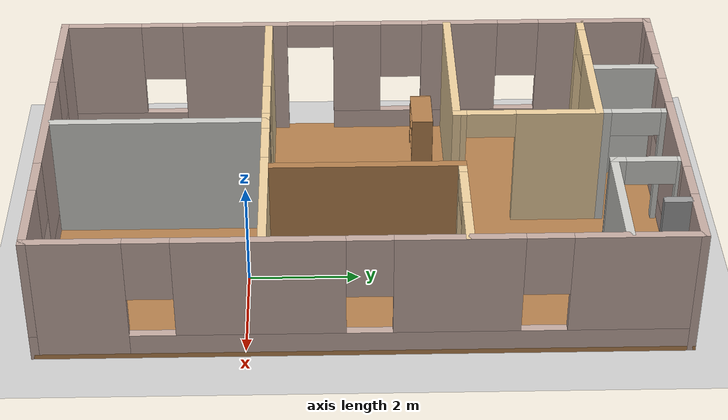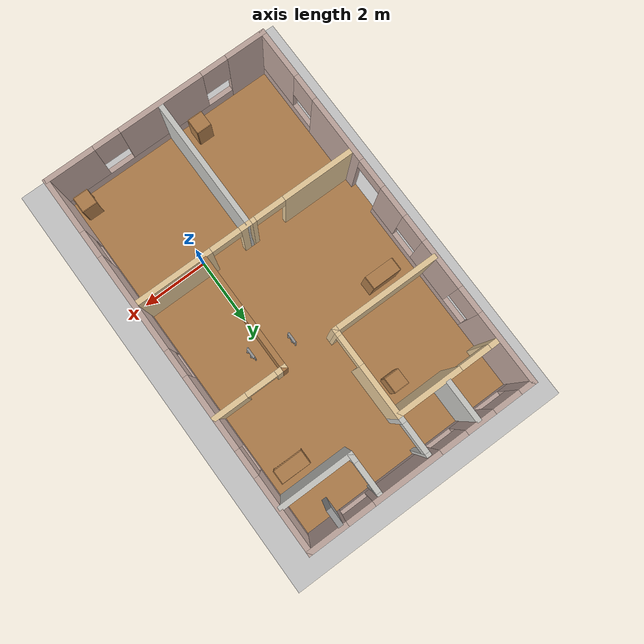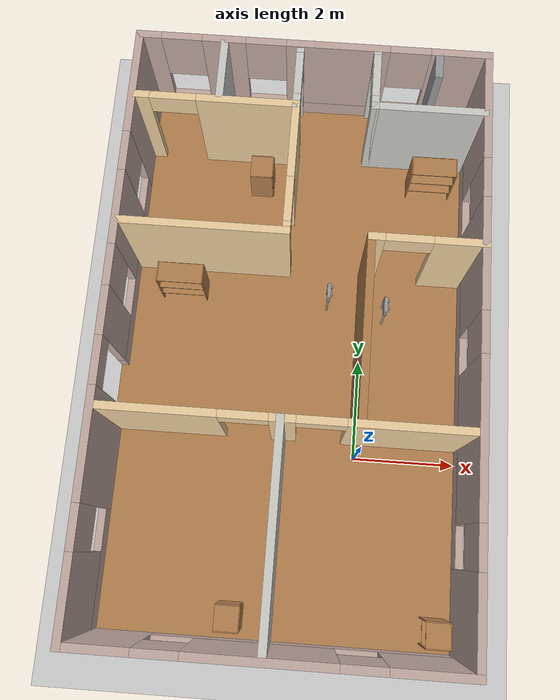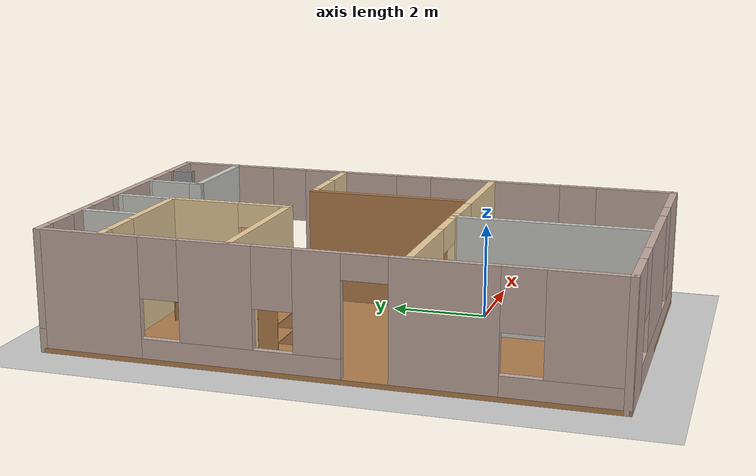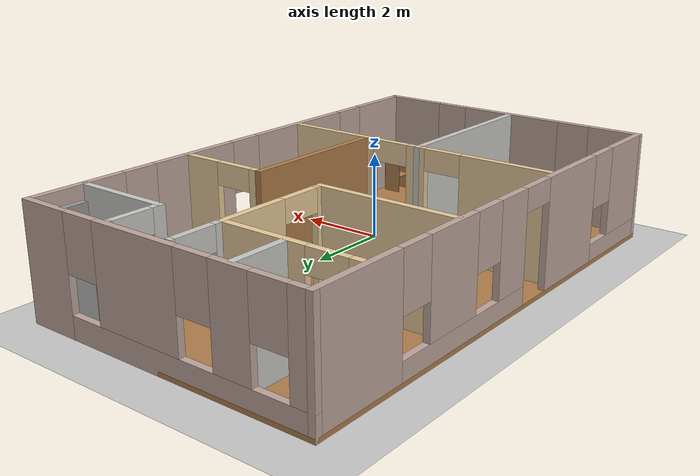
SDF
<sdf version="1.7">
 <world name="default">
  <plugin name="world_plugin" filename="libworld_plugin.so"/>
  <light name="sun" type="directional">
   <pose>0 0 10 0 -0 0</pose>
   <diffuse>0.8 0.8 0.8 1</diffuse>
   <specular>0.2 0.2 0.2 1</specular>
   <attenuation>
    <range>1000</range>
    <constant>0.9</constant>
    <linear>0.01</linear>
    <quadratic>0.001</quadratic>
   </attenuation>
   <direction>-0.5 0.1 -0.9</direction>
   <spot><inner_angle>0</inner_angle><outer_angle>0</outer_angle><falloff>0</falloff></spot>
  </light>
  <model name="ground_plane">
   <static>1</static>
   <link name="link">
    <collision name="collision">
     <geometry><plane><normal>0 0 1</normal><size>100 100</size></plane></geometry>
     <surface>
      <contact><collide_bitmask>65535</collide_bitmask></contact>
      <friction><ode><mu>100</mu><mu2>50</mu2></ode></friction>
     </surface>
    </collision>
    <visual name="visual">
     <cast_shadows>0</cast_shadows>
     <geometry><plane><normal>0 0 1</normal><size>100 100</size></plane></geometry>
     <material>
      <script><uri>file://media/materials/scripts/gazebo.material</uri><name>Gazebo/Grey</name></script>
     </material>
    </visual>
   </link>
  </model>
  <gravity>0 0 -9.8</gravity>
  <magnetic_field>6e-06 2.3e-05 -4.2e-05</magnetic_field>
  <atmosphere type="adiabatic"/>
  <physics type="ode">
   <max_step_size>0.001</max_step_size>
   <real_time_factor>1</real_time_factor>
   <real_time_update_rate>1000</real_time_update_rate>
  </physics>
  <scene><ambient>0.4 0.4 0.4 1</ambient><background>0.7 0.7 0.7 1</background><shadows>1</shadows></scene>
  <spherical_coordinates>
   <surface_model>EARTH_WGS84</surface_model>
   <latitude_deg>0</latitude_deg>
   <longitude_deg>0</longitude_deg>
   <elevation>0</elevation>
   <heading_deg>0</heading_deg>
  </spherical_coordinates>
  <model name="Building">
   <pose>4.53978 2.04826 0 0 -0 0</pose>
   <link name="Floor_1">
    <collision name="Floor_1_Collision">
     <geometry><box><size>7 11.5 0.1</size></box></geometry>
     <pose>0 0 0.05 0 -0 0</pose>
    </collision>
    <visual name="Floor_1_Visual">
     <pose>0 0 0.05 0 -0 0</pose>
     <geometry><box><size>7 11.5 0.1</size></box></geometry>
     <material>
      <script><uri>file://media/materials/scripts/gazebo.material</uri><name>Gazebo/Wood</name></script>
      <ambient>1 1 1 1</ambient>
     </material>
     <meta><layer>0</layer></meta>
    </visual>
    <pose>-5.89589 0 0 0 -0 0</pose>
   </link>
   <link name="Wall_21">
    <pose>-9.32067 -0.000135 0 0 -0 -1.5708</pose>
    <visual name="Wall_21_Visual_0">
     <pose>-4.651 0 1.25 0 -0 0</pose>
     <geometry><box><size>2.19799 0.15 2.5</size></box></geometry>
     <material>
      <script><uri>file://media/materials/scripts/gazebo.material</uri><name>Gazebo/Grey</name></script>
      <ambient>0.760784 0.662745 0.627451 1</ambient>
     </material>
     <meta><layer>0</layer></meta>
    </visual>
    <collision name="Wall_21_Collision_0">
     <geometry><box><size>2.19799 0.15 2.5</size></box></geometry>
     <pose>-4.651 0 1.25 0 -0 0</pose>
    </collision>
    <visual name="Wall_21_Visual_1">
     <pose>2.37299 0 1.25 0 -0 0</pose>
     <geometry><box><size>2.03 0.15 2.5</size></box></geometry>
     <material>
      <script><uri>file://media/materials/scripts/gazebo.material</uri><name>Gazebo/Grey</name></script>
      <ambient>0.760784 0.662745 0.627451 1</ambient>
     </material>
     <meta><layer>0</layer></meta>
    </visual>
    <collision name="Wall_21_Collision_1">
     <geometry><box><size>2.03 0.15 2.5</size></box></geometry>
     <pose>2.37299 0 1.25 0 -0 0</pose>
    </collision>
    <visual name="Wall_21_Visual_2">
     <pose>-1.54701 0 0.25 0 -0 0</pose>
     <geometry><box><size>4.01 0.15 0.5</size></box></geometry>
     <material>
      <script><uri>file://media/materials/scripts/gazebo.material</uri><name>Gazebo/Grey</name></script>
      <ambient>0.760784 0.662745 0.627451 1</ambient>
     </material>
     <meta><layer>0</layer></meta>
    </visual>
    <collision name="Wall_21_Collision_2">
     <geometry><box><size>4.01 0.15 0.5</size></box></geometry>
     <pose>-1.54701 0 0.25 0 -0 0</pose>
    </collision>
    <visual name="Wall_21_Visual_3">
     <pose>4.569 0 0.25 0 -0 0</pose>
     <geometry><box><size>2.36201 0.15 0.5</size></box></geometry>
     <material>
      <script><uri>file://media/materials/scripts/gazebo.material</uri><name>Gazebo/Grey</name></script>
      <ambient>0.760784 0.662745 0.627451 1</ambient>
     </material>
     <meta><layer>0</layer></meta>
    </visual>
    <collision name="Wall_21_Collision_3">
     <geometry><box><size>2.36201 0.15 0.5</size></box></geometry>
     <pose>4.569 0 0.25 0 -0 0</pose>
    </collision>
    <visual name="Wall_21_Visual_4">
     <pose>-2.01201 0 1.5 0 -0 0</pose>
     <geometry><box><size>1.48 0.15 2</size></box></geometry>
     <material>
      <script><uri>file://media/materials/scripts/gazebo.material</uri><name>Gazebo/Grey</name></script>
      <ambient>0.760784 0.662745 0.627451 1</ambient>
     </material>
     <meta><layer>0</layer></meta>
    </visual>
    <collision name="Wall_21_Collision_4">
     <geometry><box><size>1.48 0.15 2</size></box></geometry>
     <pose>-2.01201 0 1.5 0 -0 0</pose>
    </collision>
    <visual name="Wall_21_Visual_5">
     <pose>-0.007008 0 1.5 0 -0 0</pose>
     <geometry><box><size>0.93 0.15 2</size></box></geometry>
     <material>
      <script><uri>file://media/materials/scripts/gazebo.material</uri><name>Gazebo/Grey</name></script>
      <ambient>0.760784 0.662745 0.627451 1</ambient>
     </material>
     <meta><layer>0</layer></meta>
    </visual>
    <collision name="Wall_21_Collision_5">
     <geometry><box><size>0.93 0.15 2</size></box></geometry>
     <pose>-0.007008 0 1.5 0 -0 0</pose>
    </collision>
    <visual name="Wall_21_Visual_6">
     <pose>-0.007008 0 1.5 0 -0 0</pose>
     <geometry><box><size>0.93 0.15 2</size></box></geometry>
     <material>
      <script><uri>file://media/materials/scripts/gazebo.material</uri><name>Gazebo/Grey</name></script>
      <ambient>0.760784 0.662745 0.627451 1</ambient>
     </material>
     <meta><layer>0</layer></meta>
    </visual>
    <collision name="Wall_21_Collision_6">
     <geometry><box><size>0.93 0.15 2</size></box></geometry>
     <pose>-0.007008 0 1.5 0 -0 0</pose>
    </collision>
    <visual name="Wall_21_Visual_7">
     <pose>4.969 0 1.5 0 -0 0</pose>
     <geometry><box><size>1.56201 0.15 2</size></box></geometry>
     <material>
      <script><uri>file://media/materials/scripts/gazebo.material</uri><name>Gazebo/Grey</name></script>
      <ambient>0.760784 0.662745 0.627451 1</ambient>
     </material>
     <meta><layer>0</layer></meta>
    </visual>
    <collision name="Wall_21_Collision_7">
     <geometry><box><size>1.56201 0.15 2</size></box></geometry>
     <pose>4.969 0 1.5 0 -0 0</pose>
    </collision>
    <visual name="Wall_21_Visual_8">
     <pose>-3.15201 0 1.9 0 -0 0</pose>
     <geometry><box><size>0.8 0.15 1.2</size></box></geometry>
     <material>
      <script><uri>file://media/materials/scripts/gazebo.material</uri><name>Gazebo/Grey</name></script>
      <ambient>0.760784 0.662745 0.627451 1</ambient>
     </material>
     <meta><layer>0</layer></meta>
    </visual>
    <collision name="Wall_21_Collision_8">
     <geometry><box><size>0.8 0.15 1.2</size></box></geometry>
     <pose>-3.15201 0 1.9 0 -0 0</pose>
    </collision>
    <visual name="Wall_21_Visual_9">
     <pose>3.78799 0 1.9 0 -0 0</pose>
     <geometry><box><size>0.8 0.15 1.2</size></box></geometry>
     <material>
      <script><uri>file://media/materials/scripts/gazebo.material</uri><name>Gazebo/Grey</name></script>
      <ambient>0.760784 0.662745 0.627451 1</ambient>
     </material>
     <meta><layer>0</layer></meta>
    </visual>
    <collision name="Wall_21_Collision_9">
     <geometry><box><size>0.8 0.15 1.2</size></box></geometry>
     <pose>3.78799 0 1.9 0 -0 0</pose>
    </collision>
    <visual name="Wall_21_Visual_10">
     <pose>-0.872008 0 1.9 0 -0 0</pose>
     <geometry><box><size>0.8 0.15 1.2</size></box></geometry>
     <material>
      <script><uri>file://media/materials/scripts/gazebo.material</uri><name>Gazebo/Grey</name></script>
      <ambient>0.760784 0.662745 0.627451 1</ambient>
     </material>
     <meta><layer>0</layer></meta>
    </visual>
    <collision name="Wall_21_Collision_10">
     <geometry><box><size>0.8 0.15 1.2</size></box></geometry>
     <pose>-0.872008 0 1.9 0 -0 0</pose>
    </collision>
    <visual name="Wall_21_Visual_11">
     <pose>0.907992 0 2.25 0 -0 0</pose>
     <geometry><box><size>0.9 0.15 0.5</size></box></geometry>
     <material>
      <script><uri>file://media/materials/scripts/gazebo.material</uri><name>Gazebo/Grey</name></script>
      <ambient>0.760784 0.662745 0.627451 1</ambient>
     </material>
     <meta><layer>0</layer></meta>
    </visual>
    <collision name="Wall_21_Collision_11">
     <geometry><box><size>0.9 0.15 0.5</size></box></geometry>
     <pose>0.907992 0 2.25 0 -0 0</pose>
    </collision>
    <visual name="Wall_21_Visual_12">
     <pose>0.907992 0 2.25 0 -0 0</pose>
     <geometry><box><size>0.9 0.15 0.5</size></box></geometry>
     <material>
      <script><uri>file://media/materials/scripts/gazebo.material</uri><name>Gazebo/Grey</name></script>
      <ambient>0.760784 0.662745 0.627451 1</ambient>
     </material>
     <meta><layer>0</layer></meta>
    </visual>
    <collision name="Wall_21_Collision_12">
     <geometry><box><size>0.9 0.15 0.5</size></box></geometry>
     <pose>0.907992 0 2.25 0 -0 0</pose>
    </collision>
   </link>
   <link name="Wall_22">
    <pose>-5.89589 -5.675 0 0 -0 3.9e-05</pose>
    <visual name="Wall_22_Visual_0">
     <pose>-2.8683 0 1.25 0 -0 0</pose>
     <geometry><box><size>1.2634 0.15 2.5</size></box></geometry>
     <material>
      <script><uri>file://media/materials/scripts/gazebo.material</uri><name>Gazebo/Grey</name></script>
      <ambient>0.760784 0.662745 0.627451 1</ambient>
     </material>
     <meta><layer>0</layer></meta>
    </visual>
    <collision name="Wall_22_Collision_0">
     <geometry><box><size>1.2634 0.15 2.5</size></box></geometry>
     <pose>-2.8683 0 1.25 0 -0 0</pose>
    </collision>
    <visual name="Wall_22_Visual_1">
     <pose>0.631699 0 0.25 0 -0 0</pose>
     <geometry><box><size>5.7366 0.15 0.5</size></box></geometry>
     <material>
      <script><uri>file://media/materials/scripts/gazebo.material</uri><name>Gazebo/Grey</name></script>
      <ambient>0.760784 0.662745 0.627451 1</ambient>
     </material>
     <meta><layer>0</layer></meta>
    </visual>
    <collision name="Wall_22_Collision_1">
     <geometry><box><size>5.7366 0.15 0.5</size></box></geometry>
     <pose>0.631699 0 0.25 0 -0 0</pose>
    </collision>
    <visual name="Wall_22_Visual_2">
     <pose>-0.136711 0 1.5 0 -0 0</pose>
     <geometry><box><size>2.59978 0.15 2</size></box></geometry>
     <material>
      <script><uri>file://media/materials/scripts/gazebo.material</uri><name>Gazebo/Grey</name></script>
      <ambient>0.760784 0.662745 0.627451 1</ambient>
     </material>
     <meta><layer>0</layer></meta>
    </visual>
    <collision name="Wall_22_Collision_2">
     <geometry><box><size>2.59978 0.15 2</size></box></geometry>
     <pose>-0.136711 0 1.5 0 -0 0</pose>
    </collision>
    <visual name="Wall_22_Visual_3">
     <pose>2.73159 0 1.5 0 -0 0</pose>
     <geometry><box><size>1.53682 0.15 2</size></box></geometry>
     <material>
      <script><uri>file://media/materials/scripts/gazebo.material</uri><name>Gazebo/Grey</name></script>
      <ambient>0.760784 0.662745 0.627451 1</ambient>
     </material>
     <meta><layer>0</layer></meta>
    </visual>
    <collision name="Wall_22_Collision_3">
     <geometry><box><size>1.53682 0.15 2</size></box></geometry>
     <pose>2.73159 0 1.5 0 -0 0</pose>
    </collision>
    <visual name="Wall_22_Visual_4">
     <pose>-1.8366 0 1.9 0 -0 0</pose>
     <geometry><box><size>0.8 0.15 1.2</size></box></geometry>
     <material>
      <script><uri>file://media/materials/scripts/gazebo.material</uri><name>Gazebo/Grey</name></script>
      <ambient>0.760784 0.662745 0.627451 1</ambient>
     </material>
     <meta><layer>0</layer></meta>
    </visual>
    <collision name="Wall_22_Collision_4">
     <geometry><box><size>0.8 0.15 1.2</size></box></geometry>
     <pose>-1.8366 0 1.9 0 -0 0</pose>
    </collision>
    <visual name="Wall_22_Visual_5">
     <pose>1.56318 0 1.9 0 -0 0</pose>
     <geometry><box><size>0.8 0.15 1.2</size></box></geometry>
     <material>
      <script><uri>file://media/materials/scripts/gazebo.material</uri><name>Gazebo/Grey</name></script>
      <ambient>0.760784 0.662745 0.627451 1</ambient>
     </material>
     <meta><layer>0</layer></meta>
    </visual>
    <collision name="Wall_22_Collision_5">
     <geometry><box><size>0.8 0.15 1.2</size></box></geometry>
     <pose>1.56318 0 1.9 0 -0 0</pose>
    </collision>
   </link>
   <link name="Wall_23">
    <pose>-2.47111 0.000135 0 0 -0 1.5708</pose>
    <visual name="Wall_23_Visual_0">
     <pose>-4.889 0 1.25 0 -0 0</pose>
     <geometry><box><size>1.72201 0.15 2.5</size></box></geometry>
     <material>
      <script><uri>file://media/materials/scripts/gazebo.material</uri><name>Gazebo/Grey</name></script>
      <ambient>0.760784 0.662745 0.627451 1</ambient>
     </material>
     <meta><layer>0</layer></meta>
    </visual>
    <collision name="Wall_23_Collision_0">
     <geometry><box><size>1.72201 0.15 2.5</size></box></geometry>
     <pose>-4.889 0 1.25 0 -0 0</pose>
    </collision>
    <visual name="Wall_23_Visual_1">
     <pose>0.861004 0 0.25 0 -0 0</pose>
     <geometry><box><size>9.77799 0.15 0.5</size></box></geometry>
     <material>
      <script><uri>file://media/materials/scripts/gazebo.material</uri><name>Gazebo/Grey</name></script>
      <ambient>0.760784 0.662745 0.627451 1</ambient>
     </material>
     <meta><layer>0</layer></meta>
    </visual>
    <collision name="Wall_23_Collision_1">
     <geometry><box><size>9.77799 0.15 0.5</size></box></geometry>
     <pose>0.861004 0 0.25 0 -0 0</pose>
    </collision>
    <visual name="Wall_23_Visual_2">
     <pose>-1.76799 0 1.5 0 -0 0</pose>
     <geometry><box><size>2.92 0.15 2</size></box></geometry>
     <material>
      <script><uri>file://media/materials/scripts/gazebo.material</uri><name>Gazebo/Grey</name></script>
      <ambient>0.760784 0.662745 0.627451 1</ambient>
     </material>
     <meta><layer>0</layer></meta>
    </visual>
    <collision name="Wall_23_Collision_2">
     <geometry><box><size>2.92 0.15 2</size></box></geometry>
     <pose>-1.76799 0 1.5 0 -0 0</pose>
    </collision>
    <visual name="Wall_23_Visual_3">
     <pose>1.59201 0 1.5 0 -0 0</pose>
     <geometry><box><size>2.2 0.15 2</size></box></geometry>
     <material>
      <script><uri>file://media/materials/scripts/gazebo.material</uri><name>Gazebo/Grey</name></script>
      <ambient>0.760784 0.662745 0.627451 1</ambient>
     </material>
     <meta><layer>0</layer></meta>
    </visual>
    <collision name="Wall_23_Collision_3">
     <geometry><box><size>2.2 0.15 2</size></box></geometry>
     <pose>1.59201 0 1.5 0 -0 0</pose>
    </collision>
    <visual name="Wall_23_Visual_4">
     <pose>4.621 0 1.5 0 -0 0</pose>
     <geometry><box><size>2.25799 0.15 2</size></box></geometry>
     <material>
      <script><uri>file://media/materials/scripts/gazebo.material</uri><name>Gazebo/Grey</name></script>
      <ambient>0.760784 0.662745 0.627451 1</ambient>
     </material>
     <meta><layer>0</layer></meta>
    </visual>
    <collision name="Wall_23_Collision_4">
     <geometry><box><size>2.25799 0.15 2</size></box></geometry>
     <pose>4.621 0 1.5 0 -0 0</pose>
    </collision>
    <visual name="Wall_23_Visual_5">
     <pose>-3.62799 0 1.9 0 -0 0</pose>
     <geometry><box><size>0.8 0.15 1.2</size></box></geometry>
     <material>
      <script><uri>file://media/materials/scripts/gazebo.material</uri><name>Gazebo/Grey</name></script>
      <ambient>0.760784 0.662745 0.627451 1</ambient>
     </material>
     <meta><layer>0</layer></meta>
    </visual>
    <collision name="Wall_23_Collision_5">
     <geometry><box><size>0.8 0.15 1.2</size></box></geometry>
     <pose>-3.62799 0 1.9 0 -0 0</pose>
    </collision>
    <visual name="Wall_23_Visual_6">
     <pose>0.092008 0 1.9 0 -0 0</pose>
     <geometry><box><size>0.8 0.15 1.2</size></box></geometry>
     <material>
      <script><uri>file://media/materials/scripts/gazebo.material</uri><name>Gazebo/Grey</name></script>
      <ambient>0.760784 0.662745 0.627451 1</ambient>
     </material>
     <meta><layer>0</layer></meta>
    </visual>
    <collision name="Wall_23_Collision_6">
     <geometry><box><size>0.8 0.15 1.2</size></box></geometry>
     <pose>0.092008 0 1.9 0 -0 0</pose>
    </collision>
    <visual name="Wall_23_Visual_7">
     <pose>3.09201 0 1.9 0 -0 0</pose>
     <geometry><box><size>0.8 0.15 1.2</size></box></geometry>
     <material>
      <script><uri>file://media/materials/scripts/gazebo.material</uri><name>Gazebo/Grey</name></script>
      <ambient>0.760784 0.662745 0.627451 1</ambient>
     </material>
     <meta><layer>0</layer></meta>
    </visual>
    <collision name="Wall_23_Collision_7">
     <geometry><box><size>0.8 0.15 1.2</size></box></geometry>
     <pose>3.09201 0 1.9 0 -0 0</pose>
    </collision>
   </link>
   <link name="Wall_24">
    <pose>-5.89589 5.675 0 0 -0 -3.14155</pose>
    <visual name="Wall_24_Visual_0">
     <pose>-2.90158 0 1.25 0 -0 0</pose>
     <geometry><box><size>1.19684 0.15 2.5</size></box></geometry>
     <material>
      <script><uri>file://media/materials/scripts/gazebo.material</uri><name>Gazebo/Grey</name></script>
      <ambient>0.760784 0.662745 0.627451 1</ambient>
     </material>
     <meta><layer>0</layer></meta>
    </visual>
    <collision name="Wall_24_Collision_0">
     <geometry><box><size>1.19684 0.15 2.5</size></box></geometry>
     <pose>-2.90158 0 1.25 0 -0 0</pose>
    </collision>
    <visual name="Wall_24_Visual_1">
     <pose>0.59842 0 0.25 0 -0 0</pose>
     <geometry><box><size>5.80316 0.15 0.5</size></box></geometry>
     <material>
      <script><uri>file://media/materials/scripts/gazebo.material</uri><name>Gazebo/Grey</name></script>
      <ambient>0.760784 0.662745 0.627451 1</ambient>
     </material>
     <meta><layer>0</layer></meta>
    </visual>
    <collision name="Wall_24_Collision_1">
     <geometry><box><size>5.80316 0.15 0.5</size></box></geometry>
     <pose>0.59842 0 0.25 0 -0 0</pose>
    </collision>
    <visual name="Wall_24_Visual_2">
     <pose>-0.48325 0 1.5 0 -0 0</pose>
     <geometry><box><size>2.03982 0.15 2</size></box></geometry>
     <material>
      <script><uri>file://media/materials/scripts/gazebo.material</uri><name>Gazebo/Grey</name></script>
      <ambient>0.760784 0.662745 0.627451 1</ambient>
     </material>
     <meta><layer>0</layer></meta>
    </visual>
    <collision name="Wall_24_Collision_2">
     <geometry><box><size>2.03982 0.15 2</size></box></geometry>
     <pose>-0.48325 0 1.5 0 -0 0</pose>
    </collision>
    <visual name="Wall_24_Visual_3">
     <pose>1.76661 0 1.5 0 -0 0</pose>
     <geometry><box><size>0.859895 0.15 2</size></box></geometry>
     <material>
      <script><uri>file://media/materials/scripts/gazebo.material</uri><name>Gazebo/Grey</name></script>
      <ambient>0.760784 0.662745 0.627451 1</ambient>
     </material>
     <meta><layer>0</layer></meta>
    </visual>
    <collision name="Wall_24_Collision_3">
     <geometry><box><size>0.859895 0.15 2</size></box></geometry>
     <pose>1.76661 0 1.5 0 -0 0</pose>
    </collision>
    <visual name="Wall_24_Visual_4">
     <pose>3.24828 0 1.5 0 -0 0</pose>
     <geometry><box><size>0.503445 0.15 2</size></box></geometry>
     <material>
      <script><uri>file://media/materials/scripts/gazebo.material</uri><name>Gazebo/Grey</name></script>
      <ambient>0.760784 0.662745 0.627451 1</ambient>
     </material>
     <meta><layer>0</layer></meta>
    </visual>
    <collision name="Wall_24_Collision_4">
     <geometry><box><size>0.503445 0.15 2</size></box></geometry>
     <pose>3.24828 0 1.5 0 -0 0</pose>
    </collision>
    <visual name="Wall_24_Visual_5">
     <pose>-1.90316 0 1.9 0 -0 0</pose>
     <geometry><box><size>0.8 0.15 1.2</size></box></geometry>
     <material>
      <script><uri>file://media/materials/scripts/gazebo.material</uri><name>Gazebo/Grey</name></script>
      <ambient>0.760784 0.662745 0.627451 1</ambient>
     </material>
     <meta><layer>0</layer></meta>
    </visual>
    <collision name="Wall_24_Collision_5">
     <geometry><box><size>0.8 0.15 1.2</size></box></geometry>
     <pose>-1.90316 0 1.9 0 -0 0</pose>
    </collision>
    <visual name="Wall_24_Visual_6">
     <pose>0.93666 0 1.9 0 -0 0</pose>
     <geometry><box><size>0.8 0.15 1.2</size></box></geometry>
     <material>
      <script><uri>file://media/materials/scripts/gazebo.material</uri><name>Gazebo/Grey</name></script>
      <ambient>0.760784 0.662745 0.627451 1</ambient>
     </material>
     <meta><layer>0</layer></meta>
    </visual>
    <collision name="Wall_24_Collision_6">
     <geometry><box><size>0.8 0.15 1.2</size></box></geometry>
     <pose>0.93666 0 1.9 0 -0 0</pose>
    </collision>
    <visual name="Wall_24_Visual_7">
     <pose>2.59655 0 1.9 0 -0 0</pose>
     <geometry><box><size>0.8 0.15 1.2</size></box></geometry>
     <material>
      <script><uri>file://media/materials/scripts/gazebo.material</uri><name>Gazebo/Grey</name></script>
      <ambient>0.760784 0.662745 0.627451 1</ambient>
     </material>
     <meta><layer>0</layer></meta>
    </visual>
    <collision name="Wall_24_Collision_7">
     <geometry><box><size>0.8 0.15 1.2</size></box></geometry>
     <pose>2.59655 0 1.9 0 -0 0</pose>
    </collision>
   </link>
   <link name="Wall_25">
    <collision name="Wall_25_Collision">
     <geometry><box><size>4 0.15 2.5</size></box></geometry>
     <pose>0 0 1.25 0 -0 0</pose>
    </collision>
    <visual name="Wall_25_Visual">
     <pose>0 0 1.25 0 -0 0</pose>
     <geometry><box><size>4 0.15 2.5</size></box></geometry>
     <material>
      <script><uri>file://media/materials/scripts/gazebo.material</uri><name>Gazebo/CeilingTiled</name></script>
      <ambient>0.921569 0.807843 0.615686 1</ambient>
     </material>
     <meta><layer>0</layer></meta>
    </visual>
    <pose>-5.99543 -3.63145 0 0 -0 1.5708</pose>
   </link>
   <link name="Wall_26">
    <pose>-7.59543 -1.70645 0 0 -0 3.14159</pose>
    <visual name="Wall_26_Visual_0">
     <pose>-1.53402 0 1.25 0 -0 0</pose>
     <geometry><box><size>0.281963 0.15 2.5</size></box></geometry>
     <material>
      <script><uri>file://media/materials/scripts/gazebo.material</uri><name>Gazebo/Grey</name></script>
      <ambient>0.921569 0.807843 0.615686 1</ambient>
     </material>
     <meta><layer>0</layer></meta>
    </visual>
    <collision name="Wall_26_Collision_0">
     <geometry><box><size>0.281963 0.15 2.5</size></box></geometry>
     <pose>-1.53402 0 1.25 0 -0 0</pose>
    </collision>
    <visual name="Wall_26_Visual_1">
     <pose>0.590981 0 1.25 0 -0 0</pose>
     <geometry><box><size>2.16804 0.15 2.5</size></box></geometry>
     <material>
      <script><uri>file://media/materials/scripts/gazebo.material</uri><name>Gazebo/Grey</name></script>
      <ambient>0.921569 0.807843 0.615686 1</ambient>
     </material>
     <meta><layer>0</layer></meta>
    </visual>
    <collision name="Wall_26_Collision_1">
     <geometry><box><size>2.16804 0.15 2.5</size></box></geometry>
     <pose>0.590981 0 1.25 0 -0 0</pose>
    </collision>
    <visual name="Wall_26_Visual_2">
     <pose>-0.943037 0 2.25 0 -0 0</pose>
     <geometry><box><size>0.9 0.15 0.5</size></box></geometry>
     <material>
      <script><uri>file://media/materials/scripts/gazebo.material</uri><name>Gazebo/Grey</name></script>
      <ambient>0.921569 0.807843 0.615686 1</ambient>
     </material>
     <meta><layer>0</layer></meta>
    </visual>
    <collision name="Wall_26_Collision_2">
     <geometry><box><size>0.9 0.15 0.5</size></box></geometry>
     <pose>-0.943037 0 2.25 0 -0 0</pose>
    </collision>
   </link>
   <link name="Wall_27">
    <pose>-4.29543 -1.70645 0 0 -0 0</pose>
    <visual name="Wall_27_Visual_0">
     <pose>-1.60098 0 1.25 0 -0 0</pose>
     <geometry><box><size>0.348037 0.15 2.5</size></box></geometry>
     <material>
      <script><uri>file://media/materials/scripts/gazebo.material</uri><name>Gazebo/Grey</name></script>
      <ambient>0.921569 0.807843 0.615686 1</ambient>
     </material>
     <meta><layer>0</layer></meta>
    </visual>
    <collision name="Wall_27_Collision_0">
     <geometry><box><size>0.348037 0.15 2.5</size></box></geometry>
     <pose>-1.60098 0 1.25 0 -0 0</pose>
    </collision>
    <visual name="Wall_27_Visual_1">
     <pose>0.624018 0 1.25 0 -0 0</pose>
     <geometry><box><size>2.30196 0.15 2.5</size></box></geometry>
     <material>
      <script><uri>file://media/materials/scripts/gazebo.material</uri><name>Gazebo/Grey</name></script>
      <ambient>0.921569 0.807843 0.615686 1</ambient>
     </material>
     <meta><layer>0</layer></meta>
    </visual>
    <collision name="Wall_27_Collision_1">
     <geometry><box><size>2.30196 0.15 2.5</size></box></geometry>
     <pose>0.624018 0 1.25 0 -0 0</pose>
    </collision>
    <visual name="Wall_27_Visual_2">
     <pose>-0.976963 0 2.25 0 -0 0</pose>
     <geometry><box><size>0.9 0.15 0.5</size></box></geometry>
     <material>
      <script><uri>file://media/materials/scripts/gazebo.material</uri><name>Gazebo/Grey</name></script>
      <ambient>0.921569 0.807843 0.615686 1</ambient>
     </material>
     <meta><layer>0</layer></meta>
    </visual>
    <collision name="Wall_27_Collision_2">
     <geometry><box><size>0.9 0.15 0.5</size></box></geometry>
     <pose>-0.976963 0 2.25 0 -0 0</pose>
    </collision>
   </link>
   <link name="Wall_29">
    <pose>-7.70013 4.35813 0 0 -0 0</pose>
    <visual name="Wall_29_Visual_0">
     <pose>-1.45363 0 1.25 0 -0 0</pose>
     <geometry><box><size>0.342742 0.15 2.5</size></box></geometry>
     <material>
      <script><uri>file://media/materials/scripts/gazebo.material</uri><name>Gazebo/Grey</name></script>
      <ambient>0.921569 0.807843 0.615686 1</ambient>
     </material>
     <meta><layer>0</layer></meta>
    </visual>
    <collision name="Wall_29_Collision_0">
     <geometry><box><size>0.342742 0.15 2.5</size></box></geometry>
     <pose>-1.45363 0 1.25 0 -0 0</pose>
    </collision>
    <visual name="Wall_29_Visual_1">
     <pose>0.621371 0 1.25 0 -0 0</pose>
     <geometry><box><size>2.00726 0.15 2.5</size></box></geometry>
     <material>
      <script><uri>file://media/materials/scripts/gazebo.material</uri><name>Gazebo/Grey</name></script>
      <ambient>0.921569 0.807843 0.615686 1</ambient>
     </material>
     <meta><layer>0</layer></meta>
    </visual>
    <collision name="Wall_29_Collision_1">
     <geometry><box><size>2.00726 0.15 2.5</size></box></geometry>
     <pose>0.621371 0 1.25 0 -0 0</pose>
    </collision>
    <visual name="Wall_29_Visual_2">
     <pose>-0.832258 0 2.25 0 -0 0</pose>
     <geometry><box><size>0.9 0.15 0.5</size></box></geometry>
     <material>
      <script><uri>file://media/materials/scripts/gazebo.material</uri><name>Gazebo/Grey</name></script>
      <ambient>0.921569 0.807843 0.615686 1</ambient>
     </material>
     <meta><layer>0</layer></meta>
    </visual>
    <collision name="Wall_29_Collision_2">
     <geometry><box><size>0.9 0.15 0.5</size></box></geometry>
     <pose>-0.832258 0 2.25 0 -0 0</pose>
    </collision>
   </link>
   <link name="Wall_30">
    <pose>-6.15013 3.05813 0 0 -0 -1.5708</pose>
    <visual name="Wall_30_Visual_0">
     <pose>-0.57937 0 1.25 0 -0 0</pose>
     <geometry><box><size>1.59126 0.15 2.5</size></box></geometry>
     <material>
      <script><uri>file://media/materials/scripts/gazebo.material</uri><name>Gazebo/Grey</name></script>
      <ambient>0.921569 0.807843 0.615686 1</ambient>
     </material>
     <meta><layer>0</layer></meta>
    </visual>
    <collision name="Wall_30_Collision_0">
     <geometry><box><size>1.59126 0.15 2.5</size></box></geometry>
     <pose>-0.57937 0 1.25 0 -0 0</pose>
    </collision>
    <visual name="Wall_30_Visual_1">
     <pose>1.24563 0 1.25 0 -0 0</pose>
     <geometry><box><size>0.25874 0.15 2.5</size></box></geometry>
     <material>
      <script><uri>file://media/materials/scripts/gazebo.material</uri><name>Gazebo/Grey</name></script>
      <ambient>0.921569 0.807843 0.615686 1</ambient>
     </material>
     <meta><layer>0</layer></meta>
    </visual>
    <collision name="Wall_30_Collision_1">
     <geometry><box><size>0.25874 0.15 2.5</size></box></geometry>
     <pose>1.24563 0 1.25 0 -0 0</pose>
    </collision>
    <visual name="Wall_30_Visual_2">
     <pose>0.66626 0 2.25 0 -0 0</pose>
     <geometry><box><size>0.9 0.15 0.5</size></box></geometry>
     <material>
      <script><uri>file://media/materials/scripts/gazebo.material</uri><name>Gazebo/Grey</name></script>
      <ambient>0.921569 0.807843 0.615686 1</ambient>
     </material>
     <meta><layer>0</layer></meta>
    </visual>
    <collision name="Wall_30_Collision_2">
     <geometry><box><size>0.9 0.15 0.5</size></box></geometry>
     <pose>0.66626 0 2.25 0 -0 0</pose>
    </collision>
   </link>
   <link name="Wall_31">
    <collision name="Wall_31_Collision">
     <geometry><box><size>3.25 0.15 2.5</size></box></geometry>
     <pose>0 0 1.25 0 -0 0</pose>
    </collision>
    <visual name="Wall_31_Visual">
     <pose>0 0 1.25 0 -0 0</pose>
     <geometry><box><size>3.25 0.15 2.5</size></box></geometry>
     <material>
      <script><uri>file://media/materials/scripts/gazebo.material</uri><name>Gazebo/Grey</name></script>
      <ambient>0.921569 0.807843 0.615686 1</ambient>
     </material>
     <meta><layer>0</layer></meta>
    </visual>
    <pose>-7.70013 1.75813 0 0 -0 3.14159</pose>
   </link>
   <link name="Wall_33">
    <collision name="Wall_33_Collision">
     <geometry><box><size>1.25 0.15 2.5</size></box></geometry>
     <pose>0 0 1.25 0 -0 0</pose>
    </collision>
    <visual name="Wall_33_Visual">
     <pose>0 0 1.25 0 -0 0</pose>
     <geometry><box><size>1.25 0.15 2.5</size></box></geometry>
     <material>
      <script><uri>file://media/materials/scripts/gazebo.material</uri><name>Gazebo/CeilingTiled</name></script>
      <ambient>0.921569 0.807843 0.615686 1</ambient>
     </material>
     <meta><layer>0</layer></meta>
    </visual>
    <pose>-7.64013 5.02713 0 0 -0 -1.5708</pose>
   </link>
   <link name="Wall_37">
    <pose>-6.15013 4.93313 0 0 -0 1.5708</pose>
    <visual name="Wall_37_Visual_0">
     <pose>-0.50063 0 1.25 0 -0 0</pose>
     <geometry><box><size>0.29874 0.15 2.5</size></box></geometry>
     <material>
      <script><uri>file://media/materials/scripts/gazebo.material</uri><name>Gazebo/CeilingTiled</name></script>
      <ambient>0.921569 0.807843 0.615686 1</ambient>
     </material>
     <meta><layer>0</layer></meta>
    </visual>
    <collision name="Wall_37_Collision_0">
     <geometry><box><size>0.29874 0.15 2.5</size></box></geometry>
     <pose>-0.50063 0 1.25 0 -0 0</pose>
    </collision>
    <visual name="Wall_37_Visual_1">
     <pose>0.59937 0 1.25 0 -0 0</pose>
     <geometry><box><size>0.10126 0.15 2.5</size></box></geometry>
     <material>
      <script><uri>file://media/materials/scripts/gazebo.material</uri><name>Gazebo/CeilingTiled</name></script>
      <ambient>0.921569 0.807843 0.615686 1</ambient>
     </material>
     <meta><layer>0</layer></meta>
    </visual>
    <collision name="Wall_37_Collision_1">
     <geometry><box><size>0.10126 0.15 2.5</size></box></geometry>
     <pose>0.59937 0 1.25 0 -0 0</pose>
    </collision>
    <visual name="Wall_37_Visual_2">
     <pose>0.09874 0 2.25 0 -0 0</pose>
     <geometry><box><size>0.9 0.15 0.5</size></box></geometry>
     <material>
      <script><uri>file://media/materials/scripts/gazebo.material</uri><name>Gazebo/CeilingTiled</name></script>
      <ambient>0.921569 0.807843 0.615686 1</ambient>
     </material>
     <meta><layer>0</layer></meta>
    </visual>
    <collision name="Wall_37_Collision_2">
     <geometry><box><size>0.9 0.15 0.5</size></box></geometry>
     <pose>0.09874 0 2.25 0 -0 0</pose>
    </collision>
   </link>
   <link name="Wall_39">
    <pose>-4.63239 4.98187 0 0 -0 -1.5708</pose>
    <visual name="Wall_39_Visual_0">
     <pose>-0.5925 0 1.25 0 -0 0</pose>
     <geometry><box><size>0.065 0.15 2.5</size></box></geometry>
     <material>
      <script><uri>file://media/materials/scripts/gazebo.material</uri><name>Gazebo/CeilingTiled</name></script>
      <ambient>0.921569 0.807843 0.615686 1</ambient>
     </material>
     <meta><layer>0</layer></meta>
    </visual>
    <collision name="Wall_39_Collision_0">
     <geometry><box><size>0.065 0.15 2.5</size></box></geometry>
     <pose>-0.5925 0 1.25 0 -0 0</pose>
    </collision>
    <visual name="Wall_39_Visual_1">
     <pose>0.4825 0 1.25 0 -0 0</pose>
     <geometry><box><size>0.285 0.15 2.5</size></box></geometry>
     <material>
      <script><uri>file://media/materials/scripts/gazebo.material</uri><name>Gazebo/CeilingTiled</name></script>
      <ambient>0.921569 0.807843 0.615686 1</ambient>
     </material>
     <meta><layer>0</layer></meta>
    </visual>
    <collision name="Wall_39_Collision_1">
     <geometry><box><size>0.285 0.15 2.5</size></box></geometry>
     <pose>0.4825 0 1.25 0 -0 0</pose>
    </collision>
    <visual name="Wall_39_Visual_2">
     <pose>-0.11 0 2.25 0 -0 0</pose>
     <geometry><box><size>0.9 0.15 0.5</size></box></geometry>
     <material>
      <script><uri>file://media/materials/scripts/gazebo.material</uri><name>Gazebo/CeilingTiled</name></script>
      <ambient>0.921569 0.807843 0.615686 1</ambient>
     </material>
     <meta><layer>0</layer></meta>
    </visual>
    <collision name="Wall_39_Collision_2">
     <geometry><box><size>0.9 0.15 0.5</size></box></geometry>
     <pose>-0.11 0 2.25 0 -0 0</pose>
    </collision>
   </link>
   <link name="Wall_40">
    <collision name="Wall_40_Collision">
     <geometry><box><size>2.25 0.15 2.5</size></box></geometry>
     <pose>0 0 1.25 0 -0 0</pose>
    </collision>
    <visual name="Wall_40_Visual">
     <pose>0 0 1.25 0 -0 0</pose>
     <geometry><box><size>2.25 0.15 2.5</size></box></geometry>
     <material>
      <script><uri>file://media/materials/scripts/gazebo.material</uri><name>Gazebo/CeilingTiled</name></script>
      <ambient>0.921569 0.807843 0.615686 1</ambient>
     </material>
     <meta><layer>0</layer></meta>
    </visual>
    <pose>-3.58239 4.43187 0 0 -0 0</pose>
   </link>
   <link name="Wall_42">
    <collision name="Wall_42_Collision">
     <geometry><box><size>0.5 0.15 2.5</size></box></geometry>
     <pose>0 0 1.25 0 -0 0</pose>
    </collision>
    <visual name="Wall_42_Visual">
     <pose>0 0 1.25 0 -0 0</pose>
     <geometry><box><size>0.5 0.15 2.5</size></box></geometry>
     <material>
      <script><uri>file://media/materials/scripts/gazebo.material</uri><name>Gazebo/Grey</name></script>
      <ambient>1 1 1 1</ambient>
     </material>
     <meta><layer>0</layer></meta>
    </visual>
    <pose>-3.43239 5.37687 0 0 -0 -1.5708</pose>
   </link>
   <link name="Wall_44">
    <collision name="Wall_44_Collision">
     <geometry><box><size>3.5 0.15 2.5</size></box></geometry>
     <pose>0 0 1.25 0 -0 0</pose>
    </collision>
    <visual name="Wall_44_Visual">
     <pose>0 0 1.25 0 -0 0</pose>
     <geometry><box><size>3.5 0.15 2.5</size></box></geometry>
     <material>
      <script><uri>file://media/materials/scripts/gazebo.material</uri><name>Gazebo/Wood</name></script>
      <ambient>1 1 1 1</ambient>
     </material>
     <meta><layer>0</layer></meta>
    </visual>
    <pose>-4.57239 0.086873 0 0 -0 1.5708</pose>
   </link>
   <link name="Wall_45">
    <pose>-3.52239 1.76187 0 0 -0 0</pose>
    <visual name="Wall_45_Visual_0">
     <pose>-0.9625 0 1.25 0 -0 0</pose>
     <geometry><box><size>0.325 0.15 2.5</size></box></geometry>
     <material>
      <script><uri>file://media/materials/scripts/gazebo.material</uri><name>Gazebo/Grey</name></script>
      <ambient>0.921569 0.807843 0.615686 1</ambient>
     </material>
     <meta><layer>0</layer></meta>
    </visual>
    <collision name="Wall_45_Collision_0">
     <geometry><box><size>0.325 0.15 2.5</size></box></geometry>
     <pose>-0.9625 0 1.25 0 -0 0</pose>
    </collision>
    <visual name="Wall_45_Visual_1">
     <pose>0.6125 0 1.25 0 -0 0</pose>
     <geometry><box><size>1.025 0.15 2.5</size></box></geometry>
     <material>
      <script><uri>file://media/materials/scripts/gazebo.material</uri><name>Gazebo/Grey</name></script>
      <ambient>0.921569 0.807843 0.615686 1</ambient>
     </material>
     <meta><layer>0</layer></meta>
    </visual>
    <collision name="Wall_45_Collision_1">
     <geometry><box><size>1.025 0.15 2.5</size></box></geometry>
     <pose>0.6125 0 1.25 0 -0 0</pose>
    </collision>
    <visual name="Wall_45_Visual_2">
     <pose>-0.35 0 2.25 0 -0 0</pose>
     <geometry><box><size>0.9 0.15 0.5</size></box></geometry>
     <material>
      <script><uri>file://media/materials/scripts/gazebo.material</uri><name>Gazebo/Grey</name></script>
      <ambient>0.921569 0.807843 0.615686 1</ambient>
     </material>
     <meta><layer>0</layer></meta>
    </visual>
    <collision name="Wall_45_Collision_2">
     <geometry><box><size>0.9 0.15 0.5</size></box></geometry>
     <pose>-0.35 0 2.25 0 -0 0</pose>
    </collision>
   </link>
   <static>1</static>
  </model>
  <model name="cabinet">
   <static>1</static>
   <link name="cabinet_bottom_plate">
    <inertial>
     <pose>0 0 -1 0 -0 0</pose>
     <inertia><ixx>2.05</ixx><ixy>0</ixy><ixz>0</ixz><iyy>2.05</iyy><iyz>0</iyz><izz>2.05</izz></inertia>
     <mass>25</mass>
    </inertial>
    <collision name="cabinet_bottom_plate_geom">
     <pose>0 0 0.01 0 -0 0</pose>
     <geometry><box><size>0.45 0.45 0.02</size></box></geometry>
    </collision>
    <visual name="cabinet_bottom_plate_geom_visual">
     <pose>0 0 0.01 0 -0 0</pose>
     <geometry><box><size>0.45 0.45 0.02</size></box></geometry>
     <material>
      <script><uri>file://media/materials/scripts/gazebo.material</uri><name>Gazebo/Wood</name></script>
     </material>
    </visual>
    <collision name="cabinet_bottom_plate_geom_cabinet_back_plate">
     <pose>0.235 0 0.51 0 -0 0</pose>
     <geometry><box><size>0.02 0.45 1.02</size></box></geometry>
    </collision>
    <visual name="cabinet_bottom_plate_geom_cabinet_back_plate_visual">
     <pose>0.235 0 0.51 0 -0 0</pose>
     <geometry><box><size>0.02 0.45 1.02</size></box></geometry>
     <material>
      <script><uri>file://media/materials/scripts/gazebo.material</uri><name>Gazebo/Wood</name></script>
     </material>
    </visual>
    <collision name="cabinet_bottom_plate_geom_cabinet_left_plate">
     <pose>0 0.235 0.51 0 -0 0</pose>
     <geometry><box><size>0.45 0.02 1.02</size></box></geometry>
    </collision>
    <visual name="cabinet_bottom_plate_geom_cabinet_left_plate_visual">
     <pose>0 0.235 0.51 0 -0 0</pose>
     <geometry><box><size>0.45 0.02 1.02</size></box></geometry>
     <material>
      <script><uri>file://media/materials/scripts/gazebo.material</uri><name>Gazebo/Wood</name></script>
     </material>
    </visual>
    <collision name="cabinet_bottom_plate_geom_cabinet_middle_plate">
     <pose>0 0 0.51 0 -0 0</pose>
     <geometry><box><size>0.45 0.45 0.02</size></box></geometry>
    </collision>
    <visual name="cabinet_bottom_plate_geom_cabinet_middle_plate_visual">
     <pose>0 0 0.51 0 -0 0</pose>
     <geometry><box><size>0.45 0.45 0.02</size></box></geometry>
     <material>
      <script><uri>file://media/materials/scripts/gazebo.material</uri><name>Gazebo/Wood</name></script>
     </material>
    </visual>
    <collision name="cabinet_bottom_plate_geom_cabinet_right_plate">
     <pose>0 -0.235 0.51 0 -0 0</pose>
     <geometry><box><size>0.45 0.02 1.02</size></box></geometry>
    </collision>
    <visual name="cabinet_bottom_plate_geom_cabinet_right_plate_visual">
     <pose>0 -0.235 0.51 0 -0 0</pose>
     <geometry><box><size>0.45 0.02 1.02</size></box></geometry>
     <material>
      <script><uri>file://media/materials/scripts/gazebo.material</uri><name>Gazebo/Wood</name></script>
     </material>
    </visual>
    <collision name="cabinet_bottom_plate_geom_cabinet_top_plate">
     <pose>0 0 1.01 0 -0 0</pose>
     <geometry><box><size>0.45 0.45 0.02</size></box></geometry>
    </collision>
    <visual name="cabinet_bottom_plate_geom_cabinet_top_plate_visual">
     <pose>0 0 1.01 0 -0 0</pose>
     <geometry><box><size>0.45 0.45 0.02</size></box></geometry>
     <material>
      <script><uri>file://media/materials/scripts/gazebo.material</uri><name>Gazebo/Wood</name></script>
     </material>
    </visual>
   </link>
   <pose>1.62611 -3.15166 0 0 -0 0</pose>
  </model>
  <model name="cabinet_clone">
   <static>1</static>
   <link name="cabinet_bottom_plate">
    <inertial>
     <pose>0 0 -1 0 -0 0</pose>
     <inertia><ixx>2.05</ixx><ixy>0</ixy><ixz>0</ixz><iyy>2.05</iyy><iyz>0</iyz><izz>2.05</izz></inertia>
     <mass>25</mass>
    </inertial>
    <collision name="cabinet_bottom_plate_geom">
     <pose>0 0 0.01 0 -0 0</pose>
     <geometry><box><size>0.45 0.45 0.02</size></box></geometry>
    </collision>
    <visual name="cabinet_bottom_plate_geom_visual">
     <pose>0 0 0.01 0 -0 0</pose>
     <geometry><box><size>0.45 0.45 0.02</size></box></geometry>
     <material>
      <script><uri>file://media/materials/scripts/gazebo.material</uri><name>Gazebo/Wood</name></script>
     </material>
    </visual>
    <collision name="cabinet_bottom_plate_geom_cabinet_back_plate">
     <pose>0.235 0 0.51 0 -0 0</pose>
     <geometry><box><size>0.02 0.45 1.02</size></box></geometry>
    </collision>
    <visual name="cabinet_bottom_plate_geom_cabinet_back_plate_visual">
     <pose>0.235 0 0.51 0 -0 0</pose>
     <geometry><box><size>0.02 0.45 1.02</size></box></geometry>
     <material>
      <script><uri>file://media/materials/scripts/gazebo.material</uri><name>Gazebo/Wood</name></script>
     </material>
    </visual>
    <collision name="cabinet_bottom_plate_geom_cabinet_left_plate">
     <pose>0 0.235 0.51 0 -0 0</pose>
     <geometry><box><size>0.45 0.02 1.02</size></box></geometry>
    </collision>
    <visual name="cabinet_bottom_plate_geom_cabinet_left_plate_visual">
     <pose>0 0.235 0.51 0 -0 0</pose>
     <geometry><box><size>0.45 0.02 1.02</size></box></geometry>
     <material>
      <script><uri>file://media/materials/scripts/gazebo.material</uri><name>Gazebo/Wood</name></script>
     </material>
    </visual>
    <collision name="cabinet_bottom_plate_geom_cabinet_middle_plate">
     <pose>0 0 0.51 0 -0 0</pose>
     <geometry><box><size>0.45 0.45 0.02</size></box></geometry>
    </collision>
    <visual name="cabinet_bottom_plate_geom_cabinet_middle_plate_visual">
     <pose>0 0 0.51 0 -0 0</pose>
     <geometry><box><size>0.45 0.45 0.02</size></box></geometry>
     <material>
      <script><uri>file://media/materials/scripts/gazebo.material</uri><name>Gazebo/Wood</name></script>
     </material>
    </visual>
    <collision name="cabinet_bottom_plate_geom_cabinet_right_plate">
     <pose>0 -0.235 0.51 0 -0 0</pose>
     <geometry><box><size>0.45 0.02 1.02</size></box></geometry>
    </collision>
    <visual name="cabinet_bottom_plate_geom_cabinet_right_plate_visual">
     <pose>0 -0.235 0.51 0 -0 0</pose>
     <geometry><box><size>0.45 0.02 1.02</size></box></geometry>
     <material>
      <script><uri>file://media/materials/scripts/gazebo.material</uri><name>Gazebo/Wood</name></script>
     </material>
    </visual>
    <collision name="cabinet_bottom_plate_geom_cabinet_top_plate">
     <pose>0 0 1.01 0 -0 0</pose>
     <geometry><box><size>0.45 0.45 0.02</size></box></geometry>
    </collision>
    <visual name="cabinet_bottom_plate_geom_cabinet_top_plate_visual">
     <pose>0 0 1.01 0 -0 0</pose>
     <geometry><box><size>0.45 0.45 0.02</size></box></geometry>
     <material>
      <script><uri>file://media/materials/scripts/gazebo.material</uri><name>Gazebo/Wood</name></script>
     </material>
    </visual>
   </link>
   <pose>-2.19408 -3.12597 0 0 -0 0</pose>
  </model>
  <model name="cabinet_clone_0">
   <static>1</static>
   <link name="cabinet_bottom_plate">
    <inertial>
     <pose>0 0 -1 0 -0 0</pose>
     <inertia><ixx>2.05</ixx><ixy>0</ixy><ixz>0</ixz><iyy>2.05</iyy><iyz>0</iyz><izz>2.05</izz></inertia>
     <mass>25</mass>
    </inertial>
    <collision name="cabinet_bottom_plate_geom">
     <pose>0 0 0.01 0 -0 0</pose>
     <geometry><box><size>0.45 0.45 0.02</size></box></geometry>
    </collision>
    <visual name="cabinet_bottom_plate_geom_visual">
     <pose>0 0 0.01 0 -0 0</pose>
     <geometry><box><size>0.45 0.45 0.02</size></box></geometry>
     <material>
      <script><uri>file://media/materials/scripts/gazebo.material</uri><name>Gazebo/Wood</name></script>
     </material>
    </visual>
    <collision name="cabinet_bottom_plate_geom_cabinet_back_plate">
     <pose>0.235 0 0.51 0 -0 0</pose>
     <geometry><box><size>0.02 0.45 1.02</size></box></geometry>
    </collision>
    <visual name="cabinet_bottom_plate_geom_cabinet_back_plate_visual">
     <pose>0.235 0 0.51 0 -0 0</pose>
     <geometry><box><size>0.02 0.45 1.02</size></box></geometry>
     <material>
      <script><uri>file://media/materials/scripts/gazebo.material</uri><name>Gazebo/Wood</name></script>
     </material>
    </visual>
    <collision name="cabinet_bottom_plate_geom_cabinet_left_plate">
     <pose>0 0.235 0.51 0 -0 0</pose>
     <geometry><box><size>0.45 0.02 1.02</size></box></geometry>
    </collision>
    <visual name="cabinet_bottom_plate_geom_cabinet_left_plate_visual">
     <pose>0 0.235 0.51 0 -0 0</pose>
     <geometry><box><size>0.45 0.02 1.02</size></box></geometry>
     <material>
      <script><uri>file://media/materials/scripts/gazebo.material</uri><name>Gazebo/Wood</name></script>
     </material>
    </visual>
    <collision name="cabinet_bottom_plate_geom_cabinet_middle_plate">
     <pose>0 0 0.51 0 -0 0</pose>
     <geometry><box><size>0.45 0.45 0.02</size></box></geometry>
    </collision>
    <visual name="cabinet_bottom_plate_geom_cabinet_middle_plate_visual">
     <pose>0 0 0.51 0 -0 0</pose>
     <geometry><box><size>0.45 0.45 0.02</size></box></geometry>
     <material>
      <script><uri>file://media/materials/scripts/gazebo.material</uri><name>Gazebo/Wood</name></script>
     </material>
    </visual>
    <collision name="cabinet_bottom_plate_geom_cabinet_right_plate">
     <pose>0 -0.235 0.51 0 -0 0</pose>
     <geometry><box><size>0.45 0.02 1.02</size></box></geometry>
    </collision>
    <visual name="cabinet_bottom_plate_geom_cabinet_right_plate_visual">
     <pose>0 -0.235 0.51 0 -0 0</pose>
     <geometry><box><size>0.45 0.02 1.02</size></box></geometry>
     <material>
      <script><uri>file://media/materials/scripts/gazebo.material</uri><name>Gazebo/Wood</name></script>
     </material>
    </visual>
    <collision name="cabinet_bottom_plate_geom_cabinet_top_plate">
     <pose>0 0 1.01 0 -0 0</pose>
     <geometry><box><size>0.45 0.45 0.02</size></box></geometry>
    </collision>
    <visual name="cabinet_bottom_plate_geom_cabinet_top_plate_visual">
     <pose>0 0 1.01 0 -0 0</pose>
     <geometry><box><size>0.45 0.45 0.02</size></box></geometry>
     <material>
      <script><uri>file://media/materials/scripts/gazebo.material</uri><name>Gazebo/Wood</name></script>
     </material>
    </visual>
   </link>
   <pose>-2.27456 5.78159 0 0 -0 0</pose>
  </model>
  <model name="bookshelf">
   <static>1</static>
   <link name="link">
    <inertial><mass>1</mass></inertial>
    <collision name="back">
     <pose>0 0.005 0.6 0 -0 0</pose>
     <geometry><box><size>0.9 0.01 1.2</size></box></geometry>
    </collision>
    <visual name="visual1">
     <pose>0 0.005 0.6 0 -0 0</pose>
     <geometry><box><size>0.9 0.01 1.2</size></box></geometry>
     <material>
      <script><uri>file://media/materials/scripts/gazebo.material</uri><name>Gazebo/Wood</name></script>
     </material>
    </visual>
    <collision name="left_side">
     <pose>0.45 -0.195 0.6 0 -0 0</pose>
     <geometry><box><size>0.02 0.4 1.2</size></box></geometry>
    </collision>
    <visual name="visual2">
     <pose>0.45 -0.195 0.6 0 -0 0</pose>
     <geometry><box><size>0.02 0.4 1.2</size></box></geometry>
     <material>
      <script><uri>file://media/materials/scripts/gazebo.material</uri><name>Gazebo/Wood</name></script>
     </material>
    </visual>
    <collision name="right_side">
     <pose>-0.45 -0.195 0.6 0 -0 0</pose>
     <geometry><box><size>0.02 0.4 1.2</size></box></geometry>
    </collision>
    <visual name="visual3">
     <pose>-0.45 -0.195 0.6 0 -0 0</pose>
     <geometry><box><size>0.02 0.4 1.2</size></box></geometry>
     <material>
      <script><uri>file://media/materials/scripts/gazebo.material</uri><name>Gazebo/Wood</name></script>
     </material>
    </visual>
    <collision name="bottom">
     <pose>0 -0.195 0.03 0 -0 0</pose>
     <geometry><box><size>0.88 0.4 0.06</size></box></geometry>
    </collision>
    <visual name="visual4">
     <pose>0 -0.195 0.03 0 -0 0</pose>
     <geometry><box><size>0.88 0.4 0.06</size></box></geometry>
     <material>
      <script><uri>file://media/materials/scripts/gazebo.material</uri><name>Gazebo/Wood</name></script>
     </material>
    </visual>
    <collision name="top">
     <pose>0 -0.195 1.19 0 -0 0</pose>
     <geometry><box><size>0.88 0.4 0.02</size></box></geometry>
    </collision>
    <visual name="visual5">
     <pose>0 -0.195 1.19 0 -0 0</pose>
     <geometry><box><size>0.88 0.4 0.02</size></box></geometry>
     <material>
      <script><uri>file://media/materials/scripts/gazebo.material</uri><name>Gazebo/Wood</name></script>
     </material>
    </visual>
    <collision name="low_shelf">
     <pose>0 -0.195 0.43 0 -0 0</pose>
     <geometry><box><size>0.88 0.4 0.02</size></box></geometry>
    </collision>
    <visual name="visual6">
     <pose>0 -0.195 0.43 0 -0 0</pose>
     <geometry><box><size>0.88 0.4 0.02</size></box></geometry>
     <material>
      <script><uri>file://media/materials/scripts/gazebo.material</uri><name>Gazebo/Wood</name></script>
     </material>
    </visual>
    <collision name="high_shelf">
     <pose>0 -0.195 0.8 0 -0 0</pose>
     <geometry><box><size>0.88 0.4 0.02</size></box></geometry>
    </collision>
    <visual name="visual7">
     <pose>0 -0.195 0.8 0 -0 0</pose>
     <geometry><box><size>0.88 0.4 0.02</size></box></geometry>
     <material>
      <script><uri>file://media/materials/scripts/gazebo.material</uri><name>Gazebo/Wood</name></script>
     </material>
    </visual>
   </link>
   <pose>-3.68929 3.48271 0 0 -0 0</pose>
  </model>
  <model name="bookshelf_clone">
   <static>1</static>
   <link name="link">
    <inertial><mass>1</mass></inertial>
    <collision name="back">
     <pose>0 0.005 0.6 0 -0 0</pose>
     <geometry><box><size>0.9 0.01 1.2</size></box></geometry>
    </collision>
    <visual name="visual1">
     <pose>0 0.005 0.6 0 -0 0</pose>
     <geometry><box><size>0.9 0.01 1.2</size></box></geometry>
     <material>
      <script><uri>file://media/materials/scripts/gazebo.material</uri><name>Gazebo/Wood</name></script>
     </material>
    </visual>
    <collision name="left_side">
     <pose>0.45 -0.195 0.6 0 -0 0</pose>
     <geometry><box><size>0.02 0.4 1.2</size></box></geometry>
    </collision>
    <visual name="visual2">
     <pose>0.45 -0.195 0.6 0 -0 0</pose>
     <geometry><box><size>0.02 0.4 1.2</size></box></geometry>
     <material>
      <script><uri>file://media/materials/scripts/gazebo.material</uri><name>Gazebo/Wood</name></script>
     </material>
    </visual>
    <collision name="right_side">
     <pose>-0.45 -0.195 0.6 0 -0 0</pose>
     <geometry><box><size>0.02 0.4 1.2</size></box></geometry>
    </collision>
    <visual name="visual3">
     <pose>-0.45 -0.195 0.6 0 -0 0</pose>
     <geometry><box><size>0.02 0.4 1.2</size></box></geometry>
     <material>
      <script><uri>file://media/materials/scripts/gazebo.material</uri><name>Gazebo/Wood</name></script>
     </material>
    </visual>
    <collision name="bottom">
     <pose>0 -0.195 0.03 0 -0 0</pose>
     <geometry><box><size>0.88 0.4 0.06</size></box></geometry>
    </collision>
    <visual name="visual4">
     <pose>0 -0.195 0.03 0 -0 0</pose>
     <geometry><box><size>0.88 0.4 0.06</size></box></geometry>
     <material>
      <script><uri>file://media/materials/scripts/gazebo.material</uri><name>Gazebo/Wood</name></script>
     </material>
    </visual>
    <collision name="top">
     <pose>0 -0.195 1.19 0 -0 0</pose>
     <geometry><box><size>0.88 0.4 0.02</size></box></geometry>
    </collision>
    <visual name="visual5">
     <pose>0 -0.195 1.19 0 -0 0</pose>
     <geometry><box><size>0.88 0.4 0.02</size></box></geometry>
     <material>
      <script><uri>file://media/materials/scripts/gazebo.material</uri><name>Gazebo/Wood</name></script>
     </material>
    </visual>
    <collision name="low_shelf">
     <pose>0 -0.195 0.43 0 -0 0</pose>
     <geometry><box><size>0.88 0.4 0.02</size></box></geometry>
    </collision>
    <visual name="visual6">
     <pose>0 -0.195 0.43 0 -0 0</pose>
     <geometry><box><size>0.88 0.4 0.02</size></box></geometry>
     <material>
      <script><uri>file://media/materials/scripts/gazebo.material</uri><name>Gazebo/Wood</name></script>
     </material>
    </visual>
    <collision name="high_shelf">
     <pose>0 -0.195 0.8 0 -0 0</pose>
     <geometry><box><size>0.88 0.4 0.02</size></box></geometry>
    </collision>
    <visual name="visual7">
     <pose>0 -0.195 0.8 0 -0 0</pose>
     <geometry><box><size>0.88 0.4 0.02</size></box></geometry>
     <material>
      <script><uri>file://media/materials/scripts/gazebo.material</uri><name>Gazebo/Wood</name></script>
     </material>
    </visual>
   </link>
   <pose>1.27744 6.13406 0 0 -0 0</pose>
  </model>
  <model name="HumanoidRobot">
   <link name="link_0">
    <inertial>
     <mass>1</mass>
     <inertia><ixx>0.145833</ixx><ixy>0</ixy><ixz>0</ixz><iyy>0.145833</iyy><iyz>0</iyz><izz>0.125</izz></inertia>
    </inertial>
    <pose>-0.005 -0.16914 -0.096951 0 -0 0</pose>
    <visual name="visual">
     <geometry><cylinder><radius>0.02</radius><length>0.7</length></cylinder></geometry>
     <material>
      <lighting>1</lighting>
      <script><uri>file://media/materials/scripts/gazebo.material</uri><name>Gazebo/Grey</name></script>
      <shader type="pixel"><normal_map>__default__</normal_map></shader>
      <ambient>0.3 0.3 0.3 1</ambient>
      <diffuse>0.7 0.7 0.7 1</diffuse>
      <specular>0.01 0.01 0.01 1</specular>
      <emissive>0 0 0 1</emissive>
     </material>
    </visual>
    <collision name="collision">
     <geometry><cylinder><radius>0.02</radius><length>0.7</length></cylinder></geometry>
     <surface>
      <friction>
       <ode><mu>1</mu><mu2>1</mu2><fdir1>0 0 0</fdir1><slip1>0</slip1><slip2>0</slip2></ode>
       <torsional>
        <coefficient>1</coefficient>
        <patch_radius>0</patch_radius>
        <surface_radius>0</surface_radius>
        <use_patch_radius>1</use_patch_radius>
        <ode><slip>0</slip></ode>
       </torsional>
      </friction>
      <bounce><restitution_coefficient>0</restitution_coefficient><threshold>1e+06</threshold></bounce>
      <contact>
       <collide_without_contact>0</collide_without_contact>
       <collide_without_contact_bitmask>1</collide_without_contact_bitmask>
       <collide_bitmask>1</collide_bitmask>
       <ode>
        <soft_cfm>0</soft_cfm>
        <soft_erp>0.2</soft_erp>
        <kp>1e+13</kp>
        <kd>1</kd>
        <max_vel>0.01</max_vel>
        <min_depth>0</min_depth>
       </ode>
       <bullet>
        <split_impulse>1</split_impulse>
        <split_impulse_penetration_threshold>-0.01</split_impulse_penetration_threshold>
        <soft_cfm>0</soft_cfm>
        <soft_erp>0.2</soft_erp>
        <kp>1e+13</kp>
        <kd>1</kd>
       </bullet>
      </contact>
     </surface>
    </collision>
   </link>
   <link name="link_0_clone">
    <inertial>
     <mass>1</mass>
     <inertia><ixx>0.145833</ixx><ixy>0</ixy><ixz>0</ixz><iyy>0.145833</iyy><iyz>0</iyz><izz>0.125</izz></inertia>
    </inertial>
    <pose>-0.005 0.16957 -0.096951 0 -0 0</pose>
    <visual name="visual">
     <geometry><cylinder><radius>0.02</radius><length>0.7</length></cylinder></geometry>
     <material>
      <lighting>1</lighting>
      <script><uri>file://media/materials/scripts/gazebo.material</uri><name>Gazebo/Grey</name></script>
      <shader type="pixel"><normal_map>__default__</normal_map></shader>
      <ambient>0.3 0.3 0.3 1</ambient>
      <diffuse>0.7 0.7 0.7 1</diffuse>
      <specular>0.01 0.01 0.01 1</specular>
      <emissive>0 0 0 1</emissive>
     </material>
    </visual>
    <collision name="collision">
     <geometry><cylinder><radius>0.02</radius><length>0.7</length></cylinder></geometry>
     <surface>
      <friction>
       <ode><mu>1</mu><mu2>1</mu2><fdir1>0 0 0</fdir1><slip1>0</slip1><slip2>0</slip2></ode>
       <torsional>
        <coefficient>1</coefficient>
        <patch_radius>0</patch_radius>
        <surface_radius>0</surface_radius>
        <use_patch_radius>1</use_patch_radius>
        <ode><slip>0</slip></ode>
       </torsional>
      </friction>
      <bounce><restitution_coefficient>0</restitution_coefficient><threshold>1e+06</threshold></bounce>
      <contact>
       <collide_without_contact>0</collide_without_contact>
       <collide_without_contact_bitmask>1</collide_without_contact_bitmask>
       <collide_bitmask>1</collide_bitmask>
       <ode>
        <soft_cfm>0</soft_cfm>
        <soft_erp>0.2</soft_erp>
        <kp>1e+13</kp>
        <kd>1</kd>
        <max_vel>0.01</max_vel>
        <min_depth>0</min_depth>
       </ode>
       <bullet>
        <split_impulse>1</split_impulse>
        <split_impulse_penetration_threshold>-0.01</split_impulse_penetration_threshold>
        <soft_cfm>0</soft_cfm>
        <soft_erp>0.2</soft_erp>
        <kp>1e+13</kp>
        <kd>1</kd>
       </bullet>
      </contact>
     </surface>
    </collision>
   </link>
   <link name="link_1">
    <inertial>
     <mass>1</mass>
     <inertia>
      <ixx>0.166667</ixx>
      <ixy>0</ixy>
      <ixz>0</ixz>
      <iyy>0.166667</iyy>
      <iyz>0</iyz>
      <izz>0.166667</izz>
     </inertia>
    </inertial>
    <pose>0.01 -0.00043 0.196694 0 -0 0</pose>
    <visual name="visual">
     <geometry><box><size>0.07 0.3 0.3</size></box></geometry>
     <material>
      <lighting>1</lighting>
      <script><uri>file://media/materials/scripts/gazebo.material</uri><name>Gazebo/Grey</name></script>
      <shader type="pixel"><normal_map>__default__</normal_map></shader>
      <ambient>0.3 0.3 0.3 1</ambient>
      <diffuse>0.7 0.7 0.7 1</diffuse>
      <specular>0.01 0.01 0.01 1</specular>
      <emissive>0 0 0 1</emissive>
     </material>
    </visual>
    <collision name="collision">
     <geometry><box><size>0.07 0.3 0.3</size></box></geometry>
     <surface>
      <friction>
       <ode><mu>1</mu><mu2>1</mu2><fdir1>0 0 0</fdir1><slip1>0</slip1><slip2>0</slip2></ode>
       <torsional>
        <coefficient>1</coefficient>
        <patch_radius>0</patch_radius>
        <surface_radius>0</surface_radius>
        <use_patch_radius>1</use_patch_radius>
        <ode><slip>0</slip></ode>
       </torsional>
      </friction>
      <bounce><restitution_coefficient>0</restitution_coefficient><threshold>1e+06</threshold></bounce>
      <contact>
       <collide_without_contact>0</collide_without_contact>
       <collide_without_contact_bitmask>1</collide_without_contact_bitmask>
       <collide_bitmask>1</collide_bitmask>
       <ode>
        <soft_cfm>0</soft_cfm>
        <soft_erp>0.2</soft_erp>
        <kp>1e+13</kp>
        <kd>1</kd>
        <max_vel>0.01</max_vel>
        <min_depth>0</min_depth>
       </ode>
       <bullet>
        <split_impulse>1</split_impulse>
        <split_impulse_penetration_threshold>-0.01</split_impulse_penetration_threshold>
        <soft_cfm>0</soft_cfm>
        <soft_erp>0.2</soft_erp>
        <kp>1e+13</kp>
        <kd>1</kd>
       </bullet>
      </contact>
     </surface>
    </collision>
   </link>
   <link name="link_3">
    <inertial>
     <mass>0.000505039</mass>
     <inertia>
      <ixx>3.20326e-07</ixx>
      <ixy>0</ixy>
      <ixz>0</ixz>
      <iyy>3.20326e-07</iyy>
      <iyz>0</iyz>
      <izz>3.20326e-07</izz>
     </inertia>
    </inertial>
    <pose>0.045067 0.079776 0.268028 0 -0 0</pose>
    <visual name="visual">
     <geometry><sphere><radius>0.0398202</radius></sphere></geometry>
     <material>
      <lighting>1</lighting>
      <script><uri>file://media/materials/scripts/gazebo.material</uri><name>Gazebo/Grey</name></script>
      <shader type="pixel"/>
      <emissive>0 0 0 1</emissive>
     </material>
    </visual>
    <collision name="collision">
     <geometry><sphere><radius>0.03982</radius></sphere></geometry>
     <surface>
      <friction>
       <ode><mu>1</mu><mu2>1</mu2><fdir1>0 0 0</fdir1><slip1>0</slip1><slip2>0</slip2></ode>
       <torsional>
        <coefficient>1</coefficient>
        <patch_radius>0</patch_radius>
        <surface_radius>0</surface_radius>
        <use_patch_radius>1</use_patch_radius>
        <ode><slip>0</slip></ode>
       </torsional>
      </friction>
      <bounce><restitution_coefficient>0</restitution_coefficient><threshold>1e+06</threshold></bounce>
      <contact>
       <collide_without_contact>0</collide_without_contact>
       <collide_without_contact_bitmask>1</collide_without_contact_bitmask>
       <collide_bitmask>1</collide_bitmask>
       <ode>
        <soft_cfm>0</soft_cfm>
        <soft_erp>0.2</soft_erp>
        <kp>1e+13</kp>
        <kd>1</kd>
        <max_vel>0.01</max_vel>
        <min_depth>0</min_depth>
       </ode>
       <bullet>
        <split_impulse>1</split_impulse>
        <split_impulse_penetration_threshold>-0.01</split_impulse_penetration_threshold>
        <soft_cfm>0</soft_cfm>
        <soft_erp>0.2</soft_erp>
        <kp>1e+13</kp>
        <kd>1</kd>
       </bullet>
      </contact>
     </surface>
    </collision>
   </link>
   <link name="link_3_clone">
    <inertial>
     <mass>0.000505039</mass>
     <inertia>
      <ixx>3.20326e-07</ixx>
      <ixy>0</ixy>
      <ixz>0</ixz>
      <iyy>3.20326e-07</iyy>
      <iyz>0</iyz>
      <izz>3.20326e-07</izz>
     </inertia>
    </inertial>
    <pose>0.049349 -0.072893 0.26849 0 -0 0</pose>
    <visual name="visual">
     <geometry><sphere><radius>0.0398202</radius></sphere></geometry>
     <material>
      <lighting>1</lighting>
      <script><uri>file://media/materials/scripts/gazebo.material</uri><name>Gazebo/Grey</name></script>
      <shader type="pixel"/>
      <emissive>0 0 0 1</emissive>
     </material>
    </visual>
    <collision name="collision">
     <geometry><sphere><radius>0.03982</radius></sphere></geometry>
     <surface>
      <friction>
       <ode><mu>1</mu><mu2>1</mu2><fdir1>0 0 0</fdir1><slip1>0</slip1><slip2>0</slip2></ode>
       <torsional>
        <coefficient>1</coefficient>
        <patch_radius>0</patch_radius>
        <surface_radius>0</surface_radius>
        <use_patch_radius>1</use_patch_radius>
        <ode><slip>0</slip></ode>
       </torsional>
      </friction>
      <bounce><restitution_coefficient>0</restitution_coefficient><threshold>1e+06</threshold></bounce>
      <contact>
       <collide_without_contact>0</collide_without_contact>
       <collide_without_contact_bitmask>1</collide_without_contact_bitmask>
       <collide_bitmask>1</collide_bitmask>
       <ode>
        <soft_cfm>0</soft_cfm>
        <soft_erp>0.2</soft_erp>
        <kp>1e+13</kp>
        <kd>1</kd>
        <max_vel>0.01</max_vel>
        <min_depth>0</min_depth>
       </ode>
       <bullet>
        <split_impulse>1</split_impulse>
        <split_impulse_penetration_threshold>-0.01</split_impulse_penetration_threshold>
        <soft_cfm>0</soft_cfm>
        <soft_erp>0.2</soft_erp>
        <kp>1e+13</kp>
        <kd>1</kd>
       </bullet>
      </contact>
     </surface>
    </collision>
   </link>
   <joint name="link_1_JOINT_0" type="revolute">
    <parent>link_1</parent>
    <child>link_0_clone</child>
    <axis>
     <xyz>0 1 0</xyz>
     <limit>
      <lower>-1.79769e+308</lower>
      <upper>1.79769e+308</upper>
      <effort>-1</effort>
      <velocity>-1</velocity>
     </limit>
     <dynamics>
      <spring_reference>0</spring_reference>
      <spring_stiffness>0</spring_stiffness>
      <damping>0</damping>
     </dynamics>
    </axis>
    <physics>
     <ode><limit><cfm>0</cfm><erp>0.2</erp></limit><suspension><cfm>0</cfm><erp>0.2</erp></suspension></ode>
    </physics>
   </joint>
   <joint name="link_1_JOINT_2" type="revolute">
    <parent>link_1</parent>
    <child>link_0</child>
    <axis>
     <xyz>-0 -1 -0</xyz>
     <limit>
      <lower>-1.79769e+308</lower>
      <upper>1.79769e+308</upper>
      <effort>-1</effort>
      <velocity>-1</velocity>
     </limit>
     <dynamics>
      <spring_reference>0</spring_reference>
      <spring_stiffness>0</spring_stiffness>
      <damping>0</damping>
     </dynamics>
    </axis>
    <physics>
     <ode><limit><cfm>0</cfm><erp>0.2</erp></limit><suspension><cfm>0</cfm><erp>0.2</erp></suspension></ode>
    </physics>
   </joint>
   <joint name="link_1_JOINT_3" type="fixed">
    <parent>link_1</parent>
    <child>link_3</child>
    <physics>
     <ode><limit><cfm>0</cfm><erp>0.2</erp></limit><suspension><cfm>0</cfm><erp>0.2</erp></suspension></ode>
    </physics>
   </joint>
   <joint name="link_1_JOINT_4" type="fixed">
    <parent>link_1</parent>
    <child>link_3_clone</child>
    <physics>
     <ode><limit><cfm>0</cfm><erp>0.2</erp></limit><suspension><cfm>0</cfm><erp>0.2</erp></suspension></ode>
    </physics>
   </joint>
   <static>0</static>
   <pose>0.401512 2.92793 0.848131 0 -0 0</pose>
  </model>
  <model name="HumanoidRobot_0">
   <link name="link_0">
    <inertial>
     <mass>1</mass>
     <inertia><ixx>0.145833</ixx><ixy>0</ixy><ixz>0</ixz><iyy>0.145833</iyy><iyz>0</iyz><izz>0.125</izz></inertia>
    </inertial>
    <pose>-0.005 -0.16914 -0.096951 0 -0 0</pose>
    <visual name="visual">
     <geometry><cylinder><radius>0.02</radius><length>0.7</length></cylinder></geometry>
     <material>
      <lighting>1</lighting>
      <script><uri>file://media/materials/scripts/gazebo.material</uri><name>Gazebo/Grey</name></script>
      <shader type="pixel"><normal_map>__default__</normal_map></shader>
      <ambient>0.3 0.3 0.3 1</ambient>
      <diffuse>0.7 0.7 0.7 1</diffuse>
      <specular>0.01 0.01 0.01 1</specular>
      <emissive>0 0 0 1</emissive>
     </material>
    </visual>
    <collision name="collision">
     <geometry><cylinder><radius>0.02</radius><length>0.7</length></cylinder></geometry>
     <surface>
      <friction>
       <ode><mu>1</mu><mu2>1</mu2><fdir1>0 0 0</fdir1><slip1>0</slip1><slip2>0</slip2></ode>
       <torsional>
        <coefficient>1</coefficient>
        <patch_radius>0</patch_radius>
        <surface_radius>0</surface_radius>
        <use_patch_radius>1</use_patch_radius>
        <ode><slip>0</slip></ode>
       </torsional>
      </friction>
      <bounce><restitution_coefficient>0</restitution_coefficient><threshold>1e+06</threshold></bounce>
      <contact>
       <collide_without_contact>0</collide_without_contact>
       <collide_without_contact_bitmask>1</collide_without_contact_bitmask>
       <collide_bitmask>1</collide_bitmask>
       <ode>
        <soft_cfm>0</soft_cfm>
        <soft_erp>0.2</soft_erp>
        <kp>1e+13</kp>
        <kd>1</kd>
        <max_vel>0.01</max_vel>
        <min_depth>0</min_depth>
       </ode>
       <bullet>
        <split_impulse>1</split_impulse>
        <split_impulse_penetration_threshold>-0.01</split_impulse_penetration_threshold>
        <soft_cfm>0</soft_cfm>
        <soft_erp>0.2</soft_erp>
        <kp>1e+13</kp>
        <kd>1</kd>
       </bullet>
      </contact>
     </surface>
    </collision>
   </link>
   <link name="link_0_clone">
    <inertial>
     <mass>1</mass>
     <inertia><ixx>0.145833</ixx><ixy>0</ixy><ixz>0</ixz><iyy>0.145833</iyy><iyz>0</iyz><izz>0.125</izz></inertia>
    </inertial>
    <pose>-0.005 0.16957 -0.096951 0 -0 0</pose>
    <visual name="visual">
     <geometry><cylinder><radius>0.02</radius><length>0.7</length></cylinder></geometry>
     <material>
      <lighting>1</lighting>
      <script><uri>file://media/materials/scripts/gazebo.material</uri><name>Gazebo/Grey</name></script>
      <shader type="pixel"><normal_map>__default__</normal_map></shader>
      <ambient>0.3 0.3 0.3 1</ambient>
      <diffuse>0.7 0.7 0.7 1</diffuse>
      <specular>0.01 0.01 0.01 1</specular>
      <emissive>0 0 0 1</emissive>
     </material>
    </visual>
    <collision name="collision">
     <geometry><cylinder><radius>0.02</radius><length>0.7</length></cylinder></geometry>
     <surface>
      <friction>
       <ode><mu>1</mu><mu2>1</mu2><fdir1>0 0 0</fdir1><slip1>0</slip1><slip2>0</slip2></ode>
       <torsional>
        <coefficient>1</coefficient>
        <patch_radius>0</patch_radius>
        <surface_radius>0</surface_radius>
        <use_patch_radius>1</use_patch_radius>
        <ode><slip>0</slip></ode>
       </torsional>
      </friction>
      <bounce><restitution_coefficient>0</restitution_coefficient><threshold>1e+06</threshold></bounce>
      <contact>
       <collide_without_contact>0</collide_without_contact>
       <collide_without_contact_bitmask>1</collide_without_contact_bitmask>
       <collide_bitmask>1</collide_bitmask>
       <ode>
        <soft_cfm>0</soft_cfm>
        <soft_erp>0.2</soft_erp>
        <kp>1e+13</kp>
        <kd>1</kd>
        <max_vel>0.01</max_vel>
        <min_depth>0</min_depth>
       </ode>
       <bullet>
        <split_impulse>1</split_impulse>
        <split_impulse_penetration_threshold>-0.01</split_impulse_penetration_threshold>
        <soft_cfm>0</soft_cfm>
        <soft_erp>0.2</soft_erp>
        <kp>1e+13</kp>
        <kd>1</kd>
       </bullet>
      </contact>
     </surface>
    </collision>
   </link>
   <link name="link_1">
    <inertial>
     <mass>1</mass>
     <inertia>
      <ixx>0.166667</ixx>
      <ixy>0</ixy>
      <ixz>0</ixz>
      <iyy>0.166667</iyy>
      <iyz>0</iyz>
      <izz>0.166667</izz>
     </inertia>
    </inertial>
    <pose>0.01 -0.00043 0.196694 0 -0 0</pose>
    <visual name="visual">
     <geometry><box><size>0.07 0.3 0.3</size></box></geometry>
     <material>
      <lighting>1</lighting>
      <script><uri>file://media/materials/scripts/gazebo.material</uri><name>Gazebo/Grey</name></script>
      <shader type="pixel"><normal_map>__default__</normal_map></shader>
      <ambient>0.3 0.3 0.3 1</ambient>
      <diffuse>0.7 0.7 0.7 1</diffuse>
      <specular>0.01 0.01 0.01 1</specular>
      <emissive>0 0 0 1</emissive>
     </material>
    </visual>
    <collision name="collision">
     <geometry><box><size>0.07 0.3 0.3</size></box></geometry>
     <surface>
      <friction>
       <ode><mu>1</mu><mu2>1</mu2><fdir1>0 0 0</fdir1><slip1>0</slip1><slip2>0</slip2></ode>
       <torsional>
        <coefficient>1</coefficient>
        <patch_radius>0</patch_radius>
        <surface_radius>0</surface_radius>
        <use_patch_radius>1</use_patch_radius>
        <ode><slip>0</slip></ode>
       </torsional>
      </friction>
      <bounce><restitution_coefficient>0</restitution_coefficient><threshold>1e+06</threshold></bounce>
      <contact>
       <collide_without_contact>0</collide_without_contact>
       <collide_without_contact_bitmask>1</collide_without_contact_bitmask>
       <collide_bitmask>1</collide_bitmask>
       <ode>
        <soft_cfm>0</soft_cfm>
        <soft_erp>0.2</soft_erp>
        <kp>1e+13</kp>
        <kd>1</kd>
        <max_vel>0.01</max_vel>
        <min_depth>0</min_depth>
       </ode>
       <bullet>
        <split_impulse>1</split_impulse>
        <split_impulse_penetration_threshold>-0.01</split_impulse_penetration_threshold>
        <soft_cfm>0</soft_cfm>
        <soft_erp>0.2</soft_erp>
        <kp>1e+13</kp>
        <kd>1</kd>
       </bullet>
      </contact>
     </surface>
    </collision>
   </link>
   <link name="link_3">
    <inertial>
     <mass>0.000505039</mass>
     <inertia>
      <ixx>3.20326e-07</ixx>
      <ixy>0</ixy>
      <ixz>0</ixz>
      <iyy>3.20326e-07</iyy>
      <iyz>0</iyz>
      <izz>3.20326e-07</izz>
     </inertia>
    </inertial>
    <pose>0.045067 0.079776 0.268028 0 -0 0</pose>
    <visual name="visual">
     <geometry><sphere><radius>0.0398202</radius></sphere></geometry>
     <material>
      <lighting>1</lighting>
      <script><uri>file://media/materials/scripts/gazebo.material</uri><name>Gazebo/Grey</name></script>
      <shader type="pixel"/>
      <emissive>0 0 0 1</emissive>
     </material>
    </visual>
    <collision name="collision">
     <geometry><sphere><radius>0.03982</radius></sphere></geometry>
     <surface>
      <friction>
       <ode><mu>1</mu><mu2>1</mu2><fdir1>0 0 0</fdir1><slip1>0</slip1><slip2>0</slip2></ode>
       <torsional>
        <coefficient>1</coefficient>
        <patch_radius>0</patch_radius>
        <surface_radius>0</surface_radius>
        <use_patch_radius>1</use_patch_radius>
        <ode><slip>0</slip></ode>
       </torsional>
      </friction>
      <bounce><restitution_coefficient>0</restitution_coefficient><threshold>1e+06</threshold></bounce>
      <contact>
       <collide_without_contact>0</collide_without_contact>
       <collide_without_contact_bitmask>1</collide_without_contact_bitmask>
       <collide_bitmask>1</collide_bitmask>
       <ode>
        <soft_cfm>0</soft_cfm>
        <soft_erp>0.2</soft_erp>
        <kp>1e+13</kp>
        <kd>1</kd>
        <max_vel>0.01</max_vel>
        <min_depth>0</min_depth>
       </ode>
       <bullet>
        <split_impulse>1</split_impulse>
        <split_impulse_penetration_threshold>-0.01</split_impulse_penetration_threshold>
        <soft_cfm>0</soft_cfm>
        <soft_erp>0.2</soft_erp>
        <kp>1e+13</kp>
        <kd>1</kd>
       </bullet>
      </contact>
     </surface>
    </collision>
   </link>
   <link name="link_3_clone">
    <inertial>
     <mass>0.000505039</mass>
     <inertia>
      <ixx>3.20326e-07</ixx>
      <ixy>0</ixy>
      <ixz>0</ixz>
      <iyy>3.20326e-07</iyy>
      <iyz>0</iyz>
      <izz>3.20326e-07</izz>
     </inertia>
    </inertial>
    <pose>0.049349 -0.072893 0.26849 0 -0 0</pose>
    <visual name="visual">
     <geometry><sphere><radius>0.0398202</radius></sphere></geometry>
     <material>
      <lighting>1</lighting>
      <script><uri>file://media/materials/scripts/gazebo.material</uri><name>Gazebo/Grey</name></script>
      <shader type="pixel"/>
      <emissive>0 0 0 1</emissive>
     </material>
    </visual>
    <collision name="collision">
     <geometry><sphere><radius>0.03982</radius></sphere></geometry>
     <surface>
      <friction>
       <ode><mu>1</mu><mu2>1</mu2><fdir1>0 0 0</fdir1><slip1>0</slip1><slip2>0</slip2></ode>
       <torsional>
        <coefficient>1</coefficient>
        <patch_radius>0</patch_radius>
        <surface_radius>0</surface_radius>
        <use_patch_radius>1</use_patch_radius>
        <ode><slip>0</slip></ode>
       </torsional>
      </friction>
      <bounce><restitution_coefficient>0</restitution_coefficient><threshold>1e+06</threshold></bounce>
      <contact>
       <collide_without_contact>0</collide_without_contact>
       <collide_without_contact_bitmask>1</collide_without_contact_bitmask>
       <collide_bitmask>1</collide_bitmask>
       <ode>
        <soft_cfm>0</soft_cfm>
        <soft_erp>0.2</soft_erp>
        <kp>1e+13</kp>
        <kd>1</kd>
        <max_vel>0.01</max_vel>
        <min_depth>0</min_depth>
       </ode>
       <bullet>
        <split_impulse>1</split_impulse>
        <split_impulse_penetration_threshold>-0.01</split_impulse_penetration_threshold>
        <soft_cfm>0</soft_cfm>
        <soft_erp>0.2</soft_erp>
        <kp>1e+13</kp>
        <kd>1</kd>
       </bullet>
      </contact>
     </surface>
    </collision>
   </link>
   <joint name="link_1_JOINT_0" type="revolute">
    <parent>link_1</parent>
    <child>link_0_clone</child>
    <axis>
     <xyz>0 1 0</xyz>
     <limit>
      <lower>-1.79769e+308</lower>
      <upper>1.79769e+308</upper>
      <effort>-1</effort>
      <velocity>-1</velocity>
     </limit>
     <dynamics>
      <spring_reference>0</spring_reference>
      <spring_stiffness>0</spring_stiffness>
      <damping>0</damping>
     </dynamics>
    </axis>
    <physics>
     <ode><limit><cfm>0</cfm><erp>0.2</erp></limit><suspension><cfm>0</cfm><erp>0.2</erp></suspension></ode>
    </physics>
   </joint>
   <joint name="link_1_JOINT_2" type="revolute">
    <parent>link_1</parent>
    <child>link_0</child>
    <axis>
     <xyz>-0 -1 -0</xyz>
     <limit>
      <lower>-1.79769e+308</lower>
      <upper>1.79769e+308</upper>
      <effort>-1</effort>
      <velocity>-1</velocity>
     </limit>
     <dynamics>
      <spring_reference>0</spring_reference>
      <spring_stiffness>0</spring_stiffness>
      <damping>0</damping>
     </dynamics>
    </axis>
    <physics>
     <ode><limit><cfm>0</cfm><erp>0.2</erp></limit><suspension><cfm>0</cfm><erp>0.2</erp></suspension></ode>
    </physics>
   </joint>
   <joint name="link_1_JOINT_3" type="fixed">
    <parent>link_1</parent>
    <child>link_3</child>
    <physics>
     <ode><limit><cfm>0</cfm><erp>0.2</erp></limit><suspension><cfm>0</cfm><erp>0.2</erp></suspension></ode>
    </physics>
   </joint>
   <joint name="link_1_JOINT_4" type="fixed">
    <parent>link_1</parent>
    <child>link_3_clone</child>
    <physics>
     <ode><limit><cfm>0</cfm><erp>0.2</erp></limit><suspension><cfm>0</cfm><erp>0.2</erp></suspension></ode>
    </physics>
   </joint>
   <static>0</static>
   <pose>-0.723995 3.22388 0.578646 0 -0 0</pose>
  </model>
 </world>
</sdf>
